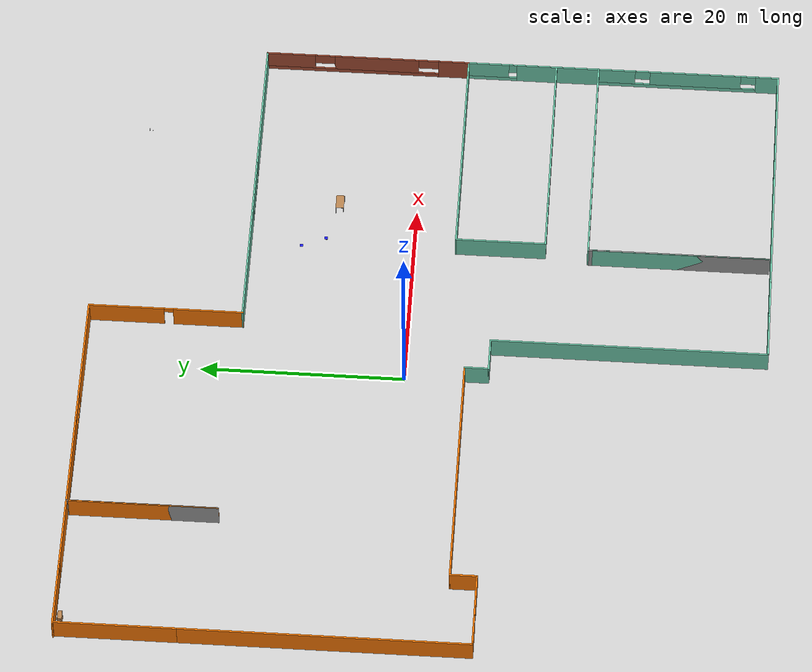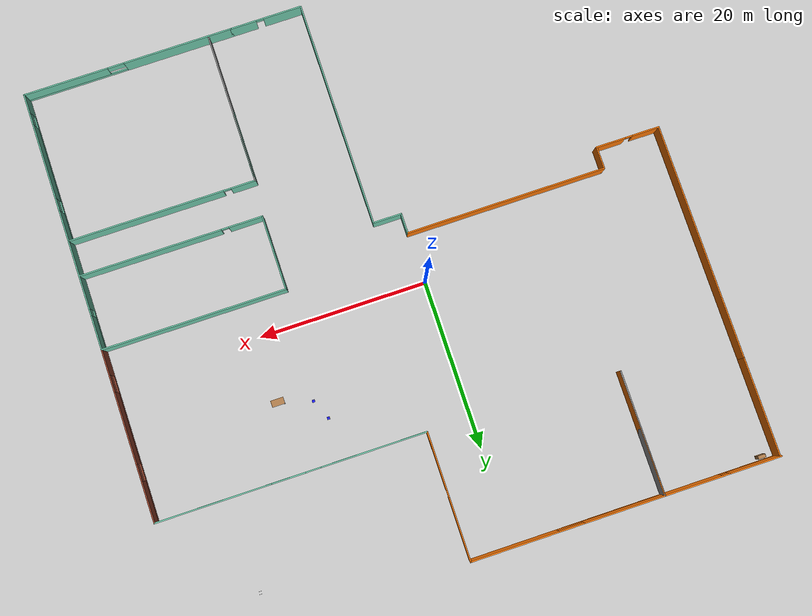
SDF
<sdf version="1.6">
 <world name="default">
  <plugin name="welcome_message" filename="libwelcome_message.so"/>
  <light name="sun" type="directional">
   <pose>0 0 10 0 -0 0</pose>
   <diffuse>0.8 0.8 0.8 1</diffuse>
   <specular>0.2 0.2 0.2 1</specular>
   <attenuation>
    <range>1000</range>
    <constant>0.9</constant>
    <linear>0.01</linear>
    <quadratic>0.001</quadratic>
   </attenuation>
   <direction>-0.5 0.1 -0.9</direction>
  </light>
  <model name="ground_plane">
   <static>1</static>
   <link name="link">
    <collision name="collision">
     <geometry><plane><normal>0 0 1</normal><size>100 100</size></plane></geometry>
     <surface>
      <contact><collide_bitmask>65535</collide_bitmask></contact>
      <friction><ode><mu>100</mu><mu2>50</mu2></ode></friction>
     </surface>
    </collision>
    <visual name="visual">
     <cast_shadows>0</cast_shadows>
     <geometry><plane><normal>0 0 1</normal><size>100 100</size></plane></geometry>
     <material>
      <script><uri>file://media/materials/scripts/gazebo.material</uri><name>Gazebo/Grey</name></script>
     </material>
    </visual>
   </link>
  </model>
  <gravity>0 0 -9.8</gravity>
  <magnetic_field>6e-06 2.3e-05 -4.2e-05</magnetic_field>
  <atmosphere type="adiabatic"/>
  <physics name="default_physics" default="0" type="ode">
   <max_step_size>0.001</max_step_size>
   <real_time_factor>1</real_time_factor>
   <real_time_update_rate>1000</real_time_update_rate>
  </physics>
  <scene><ambient>0.4 0.4 0.4 1</ambient><background>0.7 0.7 0.7 1</background><shadows>1</shadows></scene>
  <spherical_coordinates>
   <surface_model>EARTH_WGS84</surface_model>
   <latitude_deg>0</latitude_deg>
   <longitude_deg>0</longitude_deg>
   <elevation>0</elevation>
   <heading_deg>0</heading_deg>
  </spherical_coordinates>
  <model name="building1">
   <pose>2.8843 -1.97126 0 0 -0 0</pose>
   <link name="Wall_0">
    <collision name="Wall_0_Collision">
     <geometry><box><size>28.25 0.15 2.5</size></box></geometry>
     <pose>0 0 1.25 0 -0 0</pose>
    </collision>
    <visual name="Wall_0_Visual">
     <pose>0 0 1.25 0 -0 0</pose>
     <geometry><box><size>28.25 0.15 2.5</size></box></geometry>
     <material>
      <script><uri>file://media/materials/scripts/gazebo.material</uri><name>Gazebo/Grey</name></script>
      <ambient>0.996078 0.47451 0.0196078 1</ambient>
     </material>
     <meta><layer>0</layer></meta>
    </visual>
    <pose>-34.175 7.575 0 0 0 -1.5708</pose>
   </link>
   <link name="Wall_1">
    <pose>-30.375 -6.475 0 0 -0 0</pose>
    <visual name="Wall_1_Visual_0">
     <pose>-2.22971 0 1.25 0 -0 0</pose>
     <geometry><box><size>3.29058 0.15 2.5</size></box></geometry>
     <material>
      <script><uri>file://media/materials/scripts/gazebo.material</uri><name>Gazebo/Grey</name></script>
      <ambient>0.996078 0.47451 0.0196078 1</ambient>
     </material>
     <meta><layer>0</layer></meta>
    </visual>
    <collision name="Wall_1_Collision_0">
     <geometry><box><size>3.29058 0.15 2.5</size></box></geometry>
     <pose>-2.22971 0 1.25 0 -0 0</pose>
    </collision>
    <visual name="Wall_1_Visual_1">
     <pose>2.09529 0 1.25 0 -0 0</pose>
     <geometry><box><size>3.55942 0.15 2.5</size></box></geometry>
     <material>
      <script><uri>file://media/materials/scripts/gazebo.material</uri><name>Gazebo/Grey</name></script>
      <ambient>0.996078 0.47451 0.0196078 1</ambient>
     </material>
     <meta><layer>0</layer></meta>
    </visual>
    <collision name="Wall_1_Collision_1">
     <geometry><box><size>3.55942 0.15 2.5</size></box></geometry>
     <pose>2.09529 0 1.25 0 -0 0</pose>
    </collision>
    <visual name="Wall_1_Visual_2">
     <pose>-0.134418 0 2.25 0 -0 0</pose>
     <geometry><box><size>0.9 0.15 0.5</size></box></geometry>
     <material>
      <script><uri>file://media/materials/scripts/gazebo.material</uri><name>Gazebo/Grey</name></script>
      <ambient>0.996078 0.47451 0.0196078 1</ambient>
     </material>
     <meta><layer>0</layer></meta>
    </visual>
    <collision name="Wall_1_Collision_2">
     <geometry><box><size>0.9 0.15 0.5</size></box></geometry>
     <pose>-0.134418 0 2.25 0 -0 0</pose>
    </collision>
   </link>
   <link name="Wall_10">
    <pose>23.15 -15.225 0 0 -0 3.14159</pose>
    <visual name="Wall_10_Visual_0">
     <pose>-1.95259 0 1.25 0 -0 0</pose>
     <geometry><box><size>18.5948 0.15 2.5</size></box></geometry>
     <material>
      <script><uri>file://media/materials/scripts/gazebo.material</uri><name>Gazebo/Grey</name></script>
      <ambient>0.435294 0.796078 0.67451 1</ambient>
     </material>
     <meta><layer>0</layer></meta>
    </visual>
    <collision name="Wall_10_Collision_0">
     <geometry><box><size>18.5948 0.15 2.5</size></box></geometry>
     <pose>-1.95259 0 1.25 0 -0 0</pose>
    </collision>
    <visual name="Wall_10_Visual_1">
     <pose>9.74741 0 1.25 0 -0 0</pose>
     <geometry><box><size>3.00517 0.15 2.5</size></box></geometry>
     <material>
      <script><uri>file://media/materials/scripts/gazebo.material</uri><name>Gazebo/Grey</name></script>
      <ambient>0.435294 0.796078 0.67451 1</ambient>
     </material>
     <meta><layer>0</layer></meta>
    </visual>
    <collision name="Wall_10_Collision_1">
     <geometry><box><size>3.00517 0.15 2.5</size></box></geometry>
     <pose>9.74741 0 1.25 0 -0 0</pose>
    </collision>
    <visual name="Wall_10_Visual_2">
     <pose>7.79483 0 2.25 0 -0 0</pose>
     <geometry><box><size>0.9 0.15 0.5</size></box></geometry>
     <material>
      <script><uri>file://media/materials/scripts/gazebo.material</uri><name>Gazebo/Grey</name></script>
      <ambient>0.435294 0.796078 0.67451 1</ambient>
     </material>
     <meta><layer>0</layer></meta>
    </visual>
    <collision name="Wall_10_Collision_2">
     <geometry><box><size>0.9 0.15 0.5</size></box></geometry>
     <pose>7.79483 0 2.25 0 -0 0</pose>
    </collision>
   </link>
   <link name="Wall_11">
    <collision name="Wall_11_Collision">
     <geometry><box><size>18 0.15 2.5</size></box></geometry>
     <pose>0 0 1.25 0 -0 0</pose>
    </collision>
    <visual name="Wall_11_Visual">
     <pose>0 0 1.25 0 -0 0</pose>
     <geometry><box><size>18 0.15 2.5</size></box></geometry>
     <material>
      <script><uri>file://media/materials/scripts/gazebo.material</uri><name>Gazebo/Grey</name></script>
      <ambient>1 1 1 1</ambient>
     </material>
     <meta><layer>0</layer></meta>
    </visual>
    <pose>11.975 -24.15 0 0 0 -1.5708</pose>
   </link>
   <link name="Wall_12">
    <collision name="Wall_12_Collision">
     <geometry><box><size>17.5 0.15 2.5</size></box></geometry>
     <pose>0 0 1.25 0 -0 0</pose>
    </collision>
    <visual name="Wall_12_Visual">
     <pose>0 0 1.25 0 -0 0</pose>
     <geometry><box><size>17.5 0.15 2.5</size></box></geometry>
     <material>
      <script><uri>file://media/materials/scripts/gazebo.material</uri><name>Gazebo/Grey</name></script>
      <ambient>0.435294 0.796078 0.67451 1</ambient>
     </material>
     <meta><layer>0</layer></meta>
    </visual>
    <pose>11.975 -24.4 0 0 -0 1.5708</pose>
   </link>
   <link name="Wall_14">
    <pose>34.325 -8.675 0 0 -0 1.5708</pose>
    <visual name="Wall_14_Visual_0">
     <pose>-2.47216 0 1.25 0 -0 0</pose>
     <geometry><box><size>8.30568 0.15 2.5</size></box></geometry>
     <material>
      <script><uri>file://media/materials/scripts/gazebo.material</uri><name>Gazebo/Grey</name></script>
      <ambient>0.435294 0.796078 0.67451 1</ambient>
     </material>
     <meta><layer>0</layer></meta>
    </visual>
    <collision name="Wall_14_Collision_0">
     <geometry><box><size>8.30568 0.15 2.5</size></box></geometry>
     <pose>-2.47216 0 1.25 0 -0 0</pose>
    </collision>
    <visual name="Wall_14_Visual_1">
     <pose>4.15284 0 0.25 0 -0 0</pose>
     <geometry><box><size>4.94432 0.15 0.5</size></box></geometry>
     <material>
      <script><uri>file://media/materials/scripts/gazebo.material</uri><name>Gazebo/Grey</name></script>
      <ambient>0.435294 0.796078 0.67451 1</ambient>
     </material>
     <meta><layer>0</layer></meta>
    </visual>
    <collision name="Wall_14_Collision_1">
     <geometry><box><size>4.94432 0.15 0.5</size></box></geometry>
     <pose>4.15284 0 0.25 0 -0 0</pose>
    </collision>
    <visual name="Wall_14_Visual_2">
     <pose>4.55284 0 1.5 0 -0 0</pose>
     <geometry><box><size>4.14432 0.15 2</size></box></geometry>
     <material>
      <script><uri>file://media/materials/scripts/gazebo.material</uri><name>Gazebo/Grey</name></script>
      <ambient>0.435294 0.796078 0.67451 1</ambient>
     </material>
     <meta><layer>0</layer></meta>
    </visual>
    <collision name="Wall_14_Collision_2">
     <geometry><box><size>4.14432 0.15 2</size></box></geometry>
     <pose>4.55284 0 1.5 0 -0 0</pose>
    </collision>
    <visual name="Wall_14_Visual_3">
     <pose>2.08068 0 1.9 0 -0 0</pose>
     <geometry><box><size>0.8 0.15 1.2</size></box></geometry>
     <material>
      <script><uri>file://media/materials/scripts/gazebo.material</uri><name>Gazebo/Grey</name></script>
      <ambient>0.435294 0.796078 0.67451 1</ambient>
     </material>
     <meta><layer>0</layer></meta>
    </visual>
    <collision name="Wall_14_Collision_3">
     <geometry><box><size>0.8 0.15 1.2</size></box></geometry>
     <pose>2.08068 0 1.9 0 -0 0</pose>
    </collision>
   </link>
   <link name="Wall_15">
    <collision name="Wall_15_Collision">
     <geometry><box><size>22 0.15 2.5</size></box></geometry>
     <pose>0 0 1.25 0 -0 0</pose>
    </collision>
    <visual name="Wall_15_Visual">
     <pose>0 0 1.25 0 -0 0</pose>
     <geometry><box><size>22 0.15 2.5</size></box></geometry>
     <material>
      <script><uri>file://media/materials/scripts/gazebo.material</uri><name>Gazebo/Grey</name></script>
      <ambient>0.435294 0.796078 0.67451 1</ambient>
     </material>
     <meta><layer>0</layer></meta>
    </visual>
    <pose>23.4 -2.125 0 0 -0 3.14159</pose>
   </link>
   <link name="Wall_16">
    <collision name="Wall_16_Collision">
     <geometry><box><size>9 0.15 2.5</size></box></geometry>
     <pose>0 0 1.25 0 -0 0</pose>
    </collision>
    <visual name="Wall_16_Visual">
     <pose>0 0 1.25 0 -0 0</pose>
     <geometry><box><size>9 0.15 2.5</size></box></geometry>
     <material>
      <script><uri>file://media/materials/scripts/gazebo.material</uri><name>Gazebo/Grey</name></script>
      <ambient>0.435294 0.796078 0.67451 1</ambient>
     </material>
     <meta><layer>0</layer></meta>
    </visual>
    <pose>12.475 -6.55 0 0 0 -1.5708</pose>
   </link>
   <link name="Wall_17">
    <pose>23.4 -10.975 0 0 -0 0</pose>
    <visual name="Wall_17_Visual_0">
     <pose>-8.94755 0 1.25 0 -0 0</pose>
     <geometry><box><size>4.1049 0.15 2.5</size></box></geometry>
     <material>
      <script><uri>file://media/materials/scripts/gazebo.material</uri><name>Gazebo/Grey</name></script>
      <ambient>0.435294 0.796078 0.67451 1</ambient>
     </material>
     <meta><layer>0</layer></meta>
    </visual>
    <collision name="Wall_17_Collision_0">
     <geometry><box><size>4.1049 0.15 2.5</size></box></geometry>
     <pose>-8.94755 0 1.25 0 -0 0</pose>
    </collision>
    <visual name="Wall_17_Visual_1">
     <pose>2.50245 0 1.25 0 -0 0</pose>
     <geometry><box><size>16.9951 0.15 2.5</size></box></geometry>
     <material>
      <script><uri>file://media/materials/scripts/gazebo.material</uri><name>Gazebo/Grey</name></script>
      <ambient>0.435294 0.796078 0.67451 1</ambient>
     </material>
     <meta><layer>0</layer></meta>
    </visual>
    <collision name="Wall_17_Collision_1">
     <geometry><box><size>16.9951 0.15 2.5</size></box></geometry>
     <pose>2.50245 0 1.25 0 -0 0</pose>
    </collision>
    <visual name="Wall_17_Visual_2">
     <pose>-6.4451 0 2.25 0 -0 0</pose>
     <geometry><box><size>0.9 0.15 0.5</size></box></geometry>
     <material>
      <script><uri>file://media/materials/scripts/gazebo.material</uri><name>Gazebo/Grey</name></script>
      <ambient>0.435294 0.796078 0.67451 1</ambient>
     </material>
     <meta><layer>0</layer></meta>
    </visual>
    <collision name="Wall_17_Collision_2">
     <geometry><box><size>0.9 0.15 0.5</size></box></geometry>
     <pose>-6.4451 0 2.25 0 -0 0</pose>
    </collision>
   </link>
   <link name="Wall_19">
    <pose>34.325 8.05 0 0 -0 1.5708</pose>
    <visual name="Wall_19_Visual_0">
     <pose>-8.69186 0 1.25 0 -0 0</pose>
     <geometry><box><size>3.11628 0.15 2.5</size></box></geometry>
     <material>
      <script><uri>file://media/materials/scripts/gazebo.material</uri><name>Gazebo/Bricks</name></script>
      <ambient>0.435294 0.796078 0.67451 1</ambient>
     </material>
     <meta><layer>0</layer></meta>
    </visual>
    <collision name="Wall_19_Collision_0">
     <geometry><box><size>3.11628 0.15 2.5</size></box></geometry>
     <pose>-8.69186 0 1.25 0 -0 0</pose>
    </collision>
    <visual name="Wall_19_Visual_1">
     <pose>1.55814 0 0.25 0 -0 0</pose>
     <geometry><box><size>17.3837 0.15 0.5</size></box></geometry>
     <material>
      <script><uri>file://media/materials/scripts/gazebo.material</uri><name>Gazebo/Bricks</name></script>
      <ambient>0.435294 0.796078 0.67451 1</ambient>
     </material>
     <meta><layer>0</layer></meta>
    </visual>
    <collision name="Wall_19_Collision_1">
     <geometry><box><size>17.3837 0.15 0.5</size></box></geometry>
     <pose>1.55814 0 0.25 0 -0 0</pose>
    </collision>
    <visual name="Wall_19_Visual_2">
     <pose>-0.896427 0 1.5 0 -0 0</pose>
     <geometry><box><size>8.47458 0.15 2</size></box></geometry>
     <material>
      <script><uri>file://media/materials/scripts/gazebo.material</uri><name>Gazebo/Bricks</name></script>
      <ambient>0.435294 0.796078 0.67451 1</ambient>
     </material>
     <meta><layer>0</layer></meta>
    </visual>
    <collision name="Wall_19_Collision_2">
     <geometry><box><size>8.47458 0.15 2</size></box></geometry>
     <pose>-0.896427 0 1.5 0 -0 0</pose>
    </collision>
    <visual name="Wall_19_Visual_3">
     <pose>7.79543 0 1.5 0 -0 0</pose>
     <geometry><box><size>4.90914 0.15 2</size></box></geometry>
     <material>
      <script><uri>file://media/materials/scripts/gazebo.material</uri><name>Gazebo/Bricks</name></script>
      <ambient>0.435294 0.796078 0.67451 1</ambient>
     </material>
     <meta><layer>0</layer></meta>
    </visual>
    <collision name="Wall_19_Collision_3">
     <geometry><box><size>4.90914 0.15 2</size></box></geometry>
     <pose>7.79543 0 1.5 0 -0 0</pose>
    </collision>
    <visual name="Wall_19_Visual_4">
     <pose>-6.13372 0 1.9 0 -0 0</pose>
     <geometry><box><size>2 0.15 1.2</size></box></geometry>
     <material>
      <script><uri>file://media/materials/scripts/gazebo.material</uri><name>Gazebo/Bricks</name></script>
      <ambient>0.435294 0.796078 0.67451 1</ambient>
     </material>
     <meta><layer>0</layer></meta>
    </visual>
    <collision name="Wall_19_Collision_4">
     <geometry><box><size>2 0.15 1.2</size></box></geometry>
     <pose>-6.13372 0 1.9 0 -0 0</pose>
    </collision>
    <visual name="Wall_19_Visual_5">
     <pose>4.34086 0 1.9 0 -0 0</pose>
     <geometry><box><size>2 0.15 1.2</size></box></geometry>
     <material>
      <script><uri>file://media/materials/scripts/gazebo.material</uri><name>Gazebo/Bricks</name></script>
      <ambient>0.435294 0.796078 0.67451 1</ambient>
     </material>
     <meta><layer>0</layer></meta>
    </visual>
    <collision name="Wall_19_Collision_5">
     <geometry><box><size>2 0.15 1.2</size></box></geometry>
     <pose>4.34086 0 1.9 0 -0 0</pose>
    </collision>
   </link>
   <link name="Wall_2">
    <collision name="Wall_2_Collision">
     <geometry><box><size>2.75 0.15 2.5</size></box></geometry>
     <pose>0 0 1.25 0 -0 0</pose>
    </collision>
    <visual name="Wall_2_Visual">
     <pose>0 0 1.25 0 -0 0</pose>
     <geometry><box><size>2.75 0.15 2.5</size></box></geometry>
     <material>
      <script><uri>file://media/materials/scripts/gazebo.material</uri><name>Gazebo/Grey</name></script>
      <ambient>0.996078 0.47451 0.0196078 1</ambient>
     </material>
     <meta><layer>0</layer></meta>
    </visual>
    <pose>-26.575 -5.175 0 0 -0 1.5708</pose>
   </link>
   <link name="Wall_20">
    <pose>24.65 18.225 0 0 -0 3.14159</pose>
    <visual name="Wall_20_Visual_0">
     <pose>-2.88254 0 1.25 0 -0 0</pose>
     <geometry><box><size>13.7349 0.15 2.5</size></box></geometry>
     <material>
      <script><uri>file://media/materials/scripts/gazebo.material</uri><name>Gazebo/Grey</name></script>
      <ambient>0.435294 0.796078 0.67451 1</ambient>
     </material>
     <meta><layer>0</layer></meta>
    </visual>
    <collision name="Wall_20_Collision_0">
     <geometry><box><size>13.7349 0.15 2.5</size></box></geometry>
     <pose>-2.88254 0 1.25 0 -0 0</pose>
    </collision>
    <visual name="Wall_20_Visual_1">
     <pose>6.86746 0 0.25 0 -0 0</pose>
     <geometry><box><size>5.76509 0.15 0.5</size></box></geometry>
     <material>
      <script><uri>file://media/materials/scripts/gazebo.material</uri><name>Gazebo/Grey</name></script>
      <ambient>0.435294 0.796078 0.67451 1</ambient>
     </material>
     <meta><layer>0</layer></meta>
    </visual>
    <collision name="Wall_20_Collision_1">
     <geometry><box><size>5.76509 0.15 0.5</size></box></geometry>
     <pose>6.86746 0 0.25 0 -0 0</pose>
    </collision>
    <visual name="Wall_20_Visual_2">
     <pose>8.86746 0 1.5 0 -0 0</pose>
     <geometry><box><size>1.76509 0.15 2</size></box></geometry>
     <material>
      <script><uri>file://media/materials/scripts/gazebo.material</uri><name>Gazebo/Grey</name></script>
      <ambient>0.435294 0.796078 0.67451 1</ambient>
     </material>
     <meta><layer>0</layer></meta>
    </visual>
    <collision name="Wall_20_Collision_2">
     <geometry><box><size>1.76509 0.15 2</size></box></geometry>
     <pose>8.86746 0 1.5 0 -0 0</pose>
    </collision>
    <visual name="Wall_20_Visual_3">
     <pose>5.98491 0 1.9 0 -0 0</pose>
     <geometry><box><size>4 0.15 1.2</size></box></geometry>
     <material>
      <script><uri>file://media/materials/scripts/gazebo.material</uri><name>Gazebo/Grey</name></script>
      <ambient>0.435294 0.796078 0.67451 1</ambient>
     </material>
     <meta><layer>0</layer></meta>
    </visual>
    <collision name="Wall_20_Collision_3">
     <geometry><box><size>4 0.15 1.2</size></box></geometry>
     <pose>5.98491 0 1.9 0 -0 0</pose>
    </collision>
   </link>
   <link name="Wall_21">
    <collision name="Wall_21_Collision">
     <geometry><box><size>12.75 0.15 2.5</size></box></geometry>
     <pose>0 0 1.25 0 -0 0</pose>
    </collision>
    <visual name="Wall_21_Visual">
     <pose>0 0 1.25 0 -0 0</pose>
     <geometry><box><size>12.75 0.15 2.5</size></box></geometry>
     <material>
      <script><uri>file://media/materials/scripts/gazebo.material</uri><name>Gazebo/Grey</name></script>
      <ambient>0.435294 0.796078 0.67451 1</ambient>
     </material>
     <meta><layer>0</layer></meta>
    </visual>
    <pose>8.675 18.225 0 0 -0 3.14159</pose>
   </link>
   <link name="Wall_22">
    <pose>2.375 25.775 0 0 -0 1.5708</pose>
    <visual name="Wall_22_Visual_0">
     <pose>-4.18684 0 1.25 0 -0 0</pose>
     <geometry><box><size>6.87632 0.15 2.5</size></box></geometry>
     <material>
      <script><uri>file://media/materials/scripts/gazebo.material</uri><name>Gazebo/Grey</name></script>
      <ambient>0.996078 0.47451 0.0196078 1</ambient>
     </material>
     <meta><layer>0</layer></meta>
    </visual>
    <collision name="Wall_22_Collision_0">
     <geometry><box><size>6.87632 0.15 2.5</size></box></geometry>
     <pose>-4.18684 0 1.25 0 -0 0</pose>
    </collision>
    <visual name="Wall_22_Visual_1">
     <pose>3.88816 0 1.25 0 -0 0</pose>
     <geometry><box><size>7.47368 0.15 2.5</size></box></geometry>
     <material>
      <script><uri>file://media/materials/scripts/gazebo.material</uri><name>Gazebo/Grey</name></script>
      <ambient>0.996078 0.47451 0.0196078 1</ambient>
     </material>
     <meta><layer>0</layer></meta>
    </visual>
    <collision name="Wall_22_Collision_1">
     <geometry><box><size>7.47368 0.15 2.5</size></box></geometry>
     <pose>3.88816 0 1.25 0 -0 0</pose>
    </collision>
    <visual name="Wall_22_Visual_2">
     <pose>-0.298676 0 2.25 0 -0 0</pose>
     <geometry><box><size>0.9 0.15 0.5</size></box></geometry>
     <material>
      <script><uri>file://media/materials/scripts/gazebo.material</uri><name>Gazebo/Grey</name></script>
      <ambient>0.996078 0.47451 0.0196078 1</ambient>
     </material>
     <meta><layer>0</layer></meta>
    </visual>
    <collision name="Wall_22_Collision_2">
     <geometry><box><size>0.9 0.15 0.5</size></box></geometry>
     <pose>-0.298676 0 2.25 0 -0 0</pose>
    </collision>
   </link>
   <link name="Wall_23">
    <pose>-9.05 33.325 0 0 -0 3.14159</pose>
    <visual name="Wall_23_Visual_0">
     <pose>-6.28232 0 1.25 0 -0 0</pose>
     <geometry><box><size>10.4354 0.15 2.5</size></box></geometry>
     <material>
      <script><uri>file://media/materials/scripts/gazebo.material</uri><name>Gazebo/Grey</name></script>
      <ambient>0.996078 0.47451 0.0196078 1</ambient>
     </material>
     <meta><layer>0</layer></meta>
    </visual>
    <collision name="Wall_23_Collision_0">
     <geometry><box><size>10.4354 0.15 2.5</size></box></geometry>
     <pose>-6.28232 0 1.25 0 -0 0</pose>
    </collision>
    <visual name="Wall_23_Visual_1">
     <pose>5.21768 0 0.25 0 -0 0</pose>
     <geometry><box><size>12.5646 0.15 0.5</size></box></geometry>
     <material>
      <script><uri>file://media/materials/scripts/gazebo.material</uri><name>Gazebo/Grey</name></script>
      <ambient>0.996078 0.47451 0.0196078 1</ambient>
     </material>
     <meta><layer>0</layer></meta>
    </visual>
    <collision name="Wall_23_Collision_1">
     <geometry><box><size>12.5646 0.15 0.5</size></box></geometry>
     <pose>5.21768 0 0.25 0 -0 0</pose>
    </collision>
    <visual name="Wall_23_Visual_2">
     <pose>6.71768 0 1.5 0 -0 0</pose>
     <geometry><box><size>9.56464 0.15 2</size></box></geometry>
     <material>
      <script><uri>file://media/materials/scripts/gazebo.material</uri><name>Gazebo/Grey</name></script>
      <ambient>0.996078 0.47451 0.0196078 1</ambient>
     </material>
     <meta><layer>0</layer></meta>
    </visual>
    <collision name="Wall_23_Collision_2">
     <geometry><box><size>9.56464 0.15 2</size></box></geometry>
     <pose>6.71768 0 1.5 0 -0 0</pose>
    </collision>
    <visual name="Wall_23_Visual_3">
     <pose>0.435356 0 1.9 0 -0 0</pose>
     <geometry><box><size>3 0.15 1.2</size></box></geometry>
     <material>
      <script><uri>file://media/materials/scripts/gazebo.material</uri><name>Gazebo/Grey</name></script>
      <ambient>0.996078 0.47451 0.0196078 1</ambient>
     </material>
     <meta><layer>0</layer></meta>
    </visual>
    <collision name="Wall_23_Collision_3">
     <geometry><box><size>3 0.15 1.2</size></box></geometry>
     <pose>0.435356 0 1.9 0 -0 0</pose>
    </collision>
   </link>
   <link name="Wall_24">
    <collision name="Wall_24_Collision">
     <geometry><box><size>14.75 0.15 2.5</size></box></geometry>
     <pose>0 0 1.25 0 -0 0</pose>
    </collision>
    <visual name="Wall_24_Visual">
     <pose>0 0 1.25 0 -0 0</pose>
     <geometry><box><size>14.75 0.15 2.5</size></box></geometry>
     <material>
      <script><uri>file://media/materials/scripts/gazebo.material</uri><name>Gazebo/Grey</name></script>
      <ambient>1 1 1 1</ambient>
     </material>
     <meta><layer>0</layer></meta>
    </visual>
    <pose>-20.475 26.025 0 0 0 -1.5708</pose>
   </link>
   <link name="Wall_25">
    <collision name="Wall_25_Collision">
     <geometry><box><size>14.5 0.15 2.5</size></box></geometry>
     <pose>0 0 1.25 0 -0 0</pose>
    </collision>
    <visual name="Wall_25_Visual">
     <pose>0 0 1.25 0 -0 0</pose>
     <geometry><box><size>14.5 0.15 2.5</size></box></geometry>
     <material>
      <script><uri>file://media/materials/scripts/gazebo.material</uri><name>Gazebo/Grey</name></script>
      <ambient>0.996078 0.47451 0.0196078 1</ambient>
     </material>
     <meta><layer>0</layer></meta>
    </visual>
    <pose>-20.475 25.9 0 0 -0 1.5708</pose>
   </link>
   <link name="Wall_26">
    <collision name="Wall_26_Collision">
     <geometry><box><size>0.4 0.15 2.5</size></box></geometry>
     <pose>0 0 1.25 0 -0 0</pose>
    </collision>
    <visual name="Wall_26_Visual">
     <pose>0 0 1.25 0 -0 0</pose>
     <geometry><box><size>0.4 0.15 2.5</size></box></geometry>
     <material>
      <script><uri>file://media/materials/scripts/gazebo.material</uri><name>Gazebo/Grey</name></script>
      <ambient>1 1 1 1</ambient>
     </material>
     <meta><layer>0</layer></meta>
    </visual>
    <pose>-20.475 33.2 0 0 -0 1.5708</pose>
   </link>
   <link name="Wall_27">
    <pose>-27.4 33.325 0 0 -0 3.14159</pose>
    <visual name="Wall_27_Visual_0">
     <pose>-3.49206 0 1.25 0 -0 0</pose>
     <geometry><box><size>7.01587 0.15 2.5</size></box></geometry>
     <material>
      <script><uri>file://media/materials/scripts/gazebo.material</uri><name>Gazebo/Grey</name></script>
      <ambient>0.996078 0.47451 0.0196078 1</ambient>
     </material>
     <meta><layer>0</layer></meta>
    </visual>
    <collision name="Wall_27_Collision_0">
     <geometry><box><size>7.01587 0.15 2.5</size></box></geometry>
     <pose>-3.49206 0 1.25 0 -0 0</pose>
    </collision>
    <visual name="Wall_27_Visual_1">
     <pose>3.50794 0 0.25 0 -0 0</pose>
     <geometry><box><size>6.98413 0.15 0.5</size></box></geometry>
     <material>
      <script><uri>file://media/materials/scripts/gazebo.material</uri><name>Gazebo/Grey</name></script>
      <ambient>0.996078 0.47451 0.0196078 1</ambient>
     </material>
     <meta><layer>0</layer></meta>
    </visual>
    <collision name="Wall_27_Collision_1">
     <geometry><box><size>6.98413 0.15 0.5</size></box></geometry>
     <pose>3.50794 0 0.25 0 -0 0</pose>
    </collision>
    <visual name="Wall_27_Visual_2">
     <pose>3.90794 0 1.5 0 -0 0</pose>
     <geometry><box><size>6.18413 0.15 2</size></box></geometry>
     <material>
      <script><uri>file://media/materials/scripts/gazebo.material</uri><name>Gazebo/Grey</name></script>
      <ambient>0.996078 0.47451 0.0196078 1</ambient>
     </material>
     <meta><layer>0</layer></meta>
    </visual>
    <collision name="Wall_27_Collision_2">
     <geometry><box><size>6.18413 0.15 2</size></box></geometry>
     <pose>3.90794 0 1.5 0 -0 0</pose>
    </collision>
    <visual name="Wall_27_Visual_3">
     <pose>0.415874 0 1.9 0 -0 0</pose>
     <geometry><box><size>0.8 0.15 1.2</size></box></geometry>
     <material>
      <script><uri>file://media/materials/scripts/gazebo.material</uri><name>Gazebo/Grey</name></script>
      <ambient>0.996078 0.47451 0.0196078 1</ambient>
     </material>
     <meta><layer>0</layer></meta>
    </visual>
    <collision name="Wall_27_Collision_3">
     <geometry><box><size>0.8 0.15 1.2</size></box></geometry>
     <pose>0.415874 0 1.9 0 -0 0</pose>
    </collision>
   </link>
   <link name="Wall_3">
    <collision name="Wall_3_Collision">
     <geometry><box><size>24 0.15 2.5</size></box></geometry>
     <pose>0 0 1.25 0 -0 0</pose>
    </collision>
    <visual name="Wall_3_Visual">
     <pose>0 0 1.25 0 -0 0</pose>
     <geometry><box><size>24 0.15 2.5</size></box></geometry>
     <material>
      <script><uri>file://media/materials/scripts/gazebo.material</uri><name>Gazebo/Grey</name></script>
      <ambient>0.996078 0.47451 0.0196078 1</ambient>
     </material>
     <meta><layer>0</layer></meta>
    </visual>
    <pose>-14.65 -3.875 0 0 -0 0</pose>
   </link>
   <link name="Wall_30">
    <collision name="Wall_30_Collision">
     <geometry><box><size>11.75 0.15 2.5</size></box></geometry>
     <pose>0 0 1.25 0 -0 0</pose>
    </collision>
    <visual name="Wall_30_Visual">
     <pose>0 0 1.25 0 -0 0</pose>
     <geometry><box><size>11.75 0.15 2.5</size></box></geometry>
     <material>
      <script><uri>file://media/materials/scripts/gazebo.material</uri><name>Gazebo/Grey</name></script>
      <ambient>0.996078 0.47451 0.0196078 1</ambient>
     </material>
     <meta><layer>0</layer></meta>
    </visual>
    <pose>-34.175 27.425 0 0 -0 1.5708</pose>
   </link>
   <link name="Wall_4">
    <collision name="Wall_4_Collision">
     <geometry><box><size>2.5 0.15 2.5</size></box></geometry>
     <pose>0 0 1.25 0 -0 0</pose>
    </collision>
    <visual name="Wall_4_Visual">
     <pose>0 0 1.25 0 -0 0</pose>
     <geometry><box><size>2.5 0.15 2.5</size></box></geometry>
     <material>
      <script><uri>file://media/materials/scripts/gazebo.material</uri><name>Gazebo/Grey</name></script>
      <ambient>0.435294 0.796078 0.67451 1</ambient>
     </material>
     <meta><layer>0</layer></meta>
    </visual>
    <pose>-2.725 -5.05 0 0 0 -1.5708</pose>
   </link>
   <link name="Wall_5">
    <collision name="Wall_5_Collision">
     <geometry><box><size>3.5 0.15 2.5</size></box></geometry>
     <pose>0 0 1.25 0 -0 0</pose>
    </collision>
    <visual name="Wall_5_Visual">
     <pose>0 0 1.25 0 -0 0</pose>
     <geometry><box><size>3.5 0.15 2.5</size></box></geometry>
     <material>
      <script><uri>file://media/materials/scripts/gazebo.material</uri><name>Gazebo/Grey</name></script>
      <ambient>0.435294 0.796078 0.67451 1</ambient>
     </material>
     <meta><layer>0</layer></meta>
    </visual>
    <pose>-1.05 -6.225 0 0 -0 0</pose>
   </link>
   <link name="Wall_6">
    <collision name="Wall_6_Collision">
     <geometry><box><size>27.25 0.15 2.5</size></box></geometry>
     <pose>0 0 1.25 0 -0 0</pose>
    </collision>
    <visual name="Wall_6_Visual">
     <pose>0 0 1.25 0 -0 0</pose>
     <geometry><box><size>27.25 0.15 2.5</size></box></geometry>
     <material>
      <script><uri>file://media/materials/scripts/gazebo.material</uri><name>Gazebo/Grey</name></script>
      <ambient>0.435294 0.796078 0.67451 1</ambient>
     </material>
     <meta><layer>0</layer></meta>
    </visual>
    <pose>0.625002 -19.775 0 0 0 -1.5708</pose>
   </link>
   <link name="Wall_7">
    <pose>4.925 -33.325 0 0 -0 0</pose>
    <visual name="Wall_7_Visual_0">
     <pose>-2.04468 0 1.25 0 -0 0</pose>
     <geometry><box><size>4.66063 0.15 2.5</size></box></geometry>
     <material>
      <script><uri>file://media/materials/scripts/gazebo.material</uri><name>Gazebo/Grey</name></script>
      <ambient>0.435294 0.796078 0.67451 1</ambient>
     </material>
     <meta><layer>0</layer></meta>
    </visual>
    <collision name="Wall_7_Collision_0">
     <geometry><box><size>4.66063 0.15 2.5</size></box></geometry>
     <pose>-2.04468 0 1.25 0 -0 0</pose>
    </collision>
    <visual name="Wall_7_Visual_1">
     <pose>2.78031 0 1.25 0 -0 0</pose>
     <geometry><box><size>3.18937 0.15 2.5</size></box></geometry>
     <material>
      <script><uri>file://media/materials/scripts/gazebo.material</uri><name>Gazebo/Grey</name></script>
      <ambient>0.435294 0.796078 0.67451 1</ambient>
     </material>
     <meta><layer>0</layer></meta>
    </visual>
    <collision name="Wall_7_Collision_1">
     <geometry><box><size>3.18937 0.15 2.5</size></box></geometry>
     <pose>2.78031 0 1.25 0 -0 0</pose>
    </collision>
    <visual name="Wall_7_Visual_2">
     <pose>0.73563 0 2.25 0 -0 0</pose>
     <geometry><box><size>0.9 0.15 0.5</size></box></geometry>
     <material>
      <script><uri>file://media/materials/scripts/gazebo.material</uri><name>Gazebo/Grey</name></script>
      <ambient>0.435294 0.796078 0.67451 1</ambient>
     </material>
     <meta><layer>0</layer></meta>
    </visual>
    <collision name="Wall_7_Collision_2">
     <geometry><box><size>0.9 0.15 0.5</size></box></geometry>
     <pose>0.73563 0 2.25 0 -0 0</pose>
    </collision>
   </link>
   <link name="Wall_8">
    <pose>21.775 -33.325 0 0 -0 0</pose>
    <visual name="Wall_8_Visual_0">
     <pose>-6.07614 0 1.25 0 -0 0</pose>
     <geometry><box><size>13.0977 0.15 2.5</size></box></geometry>
     <material>
      <script><uri>file://media/materials/scripts/gazebo.material</uri><name>Gazebo/Grey</name></script>
      <ambient>0.435294 0.796078 0.67451 1</ambient>
     </material>
     <meta><layer>0</layer></meta>
    </visual>
    <collision name="Wall_8_Collision_0">
     <geometry><box><size>13.0977 0.15 2.5</size></box></geometry>
     <pose>-6.07614 0 1.25 0 -0 0</pose>
    </collision>
    <visual name="Wall_8_Visual_1">
     <pose>6.54886 0 0.25 0 -0 0</pose>
     <geometry><box><size>12.1523 0.15 0.5</size></box></geometry>
     <material>
      <script><uri>file://media/materials/scripts/gazebo.material</uri><name>Gazebo/Grey</name></script>
      <ambient>0.435294 0.796078 0.67451 1</ambient>
     </material>
     <meta><layer>0</layer></meta>
    </visual>
    <collision name="Wall_8_Collision_1">
     <geometry><box><size>12.1523 0.15 0.5</size></box></geometry>
     <pose>6.54886 0 0.25 0 -0 0</pose>
    </collision>
    <visual name="Wall_8_Visual_2">
     <pose>7.54886 0 1.5 0 -0 0</pose>
     <geometry><box><size>10.1523 0.15 2</size></box></geometry>
     <material>
      <script><uri>file://media/materials/scripts/gazebo.material</uri><name>Gazebo/Grey</name></script>
      <ambient>0.435294 0.796078 0.67451 1</ambient>
     </material>
     <meta><layer>0</layer></meta>
    </visual>
    <collision name="Wall_8_Collision_2">
     <geometry><box><size>10.1523 0.15 2</size></box></geometry>
     <pose>7.54886 0 1.5 0 -0 0</pose>
    </collision>
    <visual name="Wall_8_Visual_3">
     <pose>1.47272 0 1.9 0 -0 0</pose>
     <geometry><box><size>2 0.15 1.2</size></box></geometry>
     <material>
      <script><uri>file://media/materials/scripts/gazebo.material</uri><name>Gazebo/Grey</name></script>
      <ambient>0.435294 0.796078 0.67451 1</ambient>
     </material>
     <meta><layer>0</layer></meta>
    </visual>
    <collision name="Wall_8_Collision_3">
     <geometry><box><size>2 0.15 1.2</size></box></geometry>
     <pose>1.47272 0 1.9 0 -0 0</pose>
    </collision>
   </link>
   <link name="Wall_9">
    <pose>34.325 -24.275 0 0 -0 1.5708</pose>
    <visual name="Wall_9_Visual_0">
     <pose>-7.9629 0 1.25 0 -0 0</pose>
     <geometry><box><size>2.3242 0.15 2.5</size></box></geometry>
     <material>
      <script><uri>file://media/materials/scripts/gazebo.material</uri><name>Gazebo/Grey</name></script>
      <ambient>0.435294 0.796078 0.67451 1</ambient>
     </material>
     <meta><layer>0</layer></meta>
    </visual>
    <collision name="Wall_9_Collision_0">
     <geometry><box><size>2.3242 0.15 2.5</size></box></geometry>
     <pose>-7.9629 0 1.25 0 -0 0</pose>
    </collision>
    <visual name="Wall_9_Visual_1">
     <pose>1.1621 0 0.25 0 -0 0</pose>
     <geometry><box><size>15.9258 0.15 0.5</size></box></geometry>
     <material>
      <script><uri>file://media/materials/scripts/gazebo.material</uri><name>Gazebo/Grey</name></script>
      <ambient>0.435294 0.796078 0.67451 1</ambient>
     </material>
     <meta><layer>0</layer></meta>
    </visual>
    <collision name="Wall_9_Collision_1">
     <geometry><box><size>15.9258 0.15 0.5</size></box></geometry>
     <pose>1.1621 0 0.25 0 -0 0</pose>
    </collision>
    <visual name="Wall_9_Visual_2">
     <pose>-0.731672 0 1.5 0 -0 0</pose>
     <geometry><box><size>9.13825 0.15 2</size></box></geometry>
     <material>
      <script><uri>file://media/materials/scripts/gazebo.material</uri><name>Gazebo/Grey</name></script>
      <ambient>0.435294 0.796078 0.67451 1</ambient>
     </material>
     <meta><layer>0</layer></meta>
    </visual>
    <collision name="Wall_9_Collision_2">
     <geometry><box><size>9.13825 0.15 2</size></box></geometry>
     <pose>-0.731672 0 1.5 0 -0 0</pose>
    </collision>
    <visual name="Wall_9_Visual_3">
     <pose>7.23123 0 1.5 0 -0 0</pose>
     <geometry><box><size>3.78755 0.15 2</size></box></geometry>
     <material>
      <script><uri>file://media/materials/scripts/gazebo.material</uri><name>Gazebo/Grey</name></script>
      <ambient>0.435294 0.796078 0.67451 1</ambient>
     </material>
     <meta><layer>0</layer></meta>
    </visual>
    <collision name="Wall_9_Collision_3">
     <geometry><box><size>3.78755 0.15 2</size></box></geometry>
     <pose>7.23123 0 1.5 0 -0 0</pose>
    </collision>
    <visual name="Wall_9_Visual_4">
     <pose>-6.0508 0 1.9 0 -0 0</pose>
     <geometry><box><size>1.5 0.15 1.2</size></box></geometry>
     <material>
      <script><uri>file://media/materials/scripts/gazebo.material</uri><name>Gazebo/Grey</name></script>
      <ambient>0.435294 0.796078 0.67451 1</ambient>
     </material>
     <meta><layer>0</layer></meta>
    </visual>
    <collision name="Wall_9_Collision_4">
     <geometry><box><size>1.5 0.15 1.2</size></box></geometry>
     <pose>-6.0508 0 1.9 0 -0 0</pose>
    </collision>
    <visual name="Wall_9_Visual_5">
     <pose>4.58745 0 1.9 0 -0 0</pose>
     <geometry><box><size>1.5 0.15 1.2</size></box></geometry>
     <material>
      <script><uri>file://media/materials/scripts/gazebo.material</uri><name>Gazebo/Grey</name></script>
      <ambient>0.435294 0.796078 0.67451 1</ambient>
     </material>
     <meta><layer>0</layer></meta>
    </visual>
    <collision name="Wall_9_Collision_5">
     <geometry><box><size>1.5 0.15 1.2</size></box></geometry>
     <pose>4.58745 0 1.9 0 -0 0</pose>
    </collision>
   </link>
   <static>1</static>
  </model>
  <model name="robot1">
   <link name="link_5">
    <pose>32.8439 32.9677 0.5 1.5707 -0 0</pose>
    <inertial>
     <mass>1</mass>
     <inertia><ixx>0.145833</ixx><ixy>0</ixy><ixz>0</ixz><iyy>0.145833</iyy><iyz>0</iyz><izz>0.125</izz></inertia>
    </inertial>
    <visual name="visual">
     <geometry><cylinder><radius>0.05</radius><length>0.02</length></cylinder></geometry>
     <material>
      <lighting>1</lighting>
      <script><uri>file://media/materials/scripts/gazebo.material</uri><name>Gazebo/Grey</name></script>
      <shader type="pixel"><normal_map>__default__</normal_map></shader>
      <ambient>0.3 0.3 0.3 1</ambient>
      <diffuse>0.7 0.7 0.7 1</diffuse>
      <specular>0.01 0.01 0.01 1</specular>
      <emissive>0 0 0 1</emissive>
     </material>
    </visual>
    <collision name="collision">
     <geometry><cylinder><radius>0.05</radius><length>0.02</length></cylinder></geometry>
     <surface>
      <friction>
       <ode><mu>1</mu><mu2>1</mu2><fdir1>0 0 0</fdir1><slip1>0</slip1><slip2>0</slip2></ode>
       <torsional>
        <coefficient>1</coefficient>
        <patch_radius>0</patch_radius>
        <surface_radius>0</surface_radius>
        <use_patch_radius>1</use_patch_radius>
        <ode><slip>0</slip></ode>
       </torsional>
      </friction>
      <bounce><restitution_coefficient>0</restitution_coefficient><threshold>1e+06</threshold></bounce>
      <contact>
       <collide_without_contact>0</collide_without_contact>
       <collide_without_contact_bitmask>1</collide_without_contact_bitmask>
       <collide_bitmask>1</collide_bitmask>
       <ode>
        <soft_cfm>0</soft_cfm>
        <soft_erp>0.2</soft_erp>
        <kp>1e+13</kp>
        <kd>1</kd>
        <max_vel>0.01</max_vel>
        <min_depth>0</min_depth>
       </ode>
       <bullet>
        <split_impulse>1</split_impulse>
        <split_impulse_penetration_threshold>-0.01</split_impulse_penetration_threshold>
        <soft_cfm>0</soft_cfm>
        <soft_erp>0.2</soft_erp>
        <kp>1e+13</kp>
        <kd>1</kd>
       </bullet>
      </contact>
     </surface>
    </collision>
   </link>
   <link name="link_5_clone">
    <pose>32.8439 33.2877 0.5 1.5707 -0 0</pose>
    <inertial>
     <mass>1</mass>
     <inertia><ixx>0.145833</ixx><ixy>0</ixy><ixz>0</ixz><iyy>0.145833</iyy><iyz>0</iyz><izz>0.125</izz></inertia>
    </inertial>
    <visual name="visual">
     <geometry><cylinder><radius>0.05</radius><length>0.02</length></cylinder></geometry>
     <material>
      <lighting>1</lighting>
      <script><uri>file://media/materials/scripts/gazebo.material</uri><name>Gazebo/Grey</name></script>
      <shader type="pixel"><normal_map>__default__</normal_map></shader>
      <ambient>0.3 0.3 0.3 1</ambient>
      <diffuse>0.7 0.7 0.7 1</diffuse>
      <specular>0.01 0.01 0.01 1</specular>
      <emissive>0 0 0 1</emissive>
     </material>
    </visual>
    <collision name="collision">
     <geometry><cylinder><radius>0.05</radius><length>0.02</length></cylinder></geometry>
     <surface>
      <friction>
       <ode><mu>1</mu><mu2>1</mu2><fdir1>0 0 0</fdir1><slip1>0</slip1><slip2>0</slip2></ode>
       <torsional>
        <coefficient>1</coefficient>
        <patch_radius>0</patch_radius>
        <surface_radius>0</surface_radius>
        <use_patch_radius>1</use_patch_radius>
        <ode><slip>0</slip></ode>
       </torsional>
      </friction>
      <bounce><restitution_coefficient>0</restitution_coefficient><threshold>1e+06</threshold></bounce>
      <contact>
       <collide_without_contact>0</collide_without_contact>
       <collide_without_contact_bitmask>1</collide_without_contact_bitmask>
       <collide_bitmask>1</collide_bitmask>
       <ode>
        <soft_cfm>0</soft_cfm>
        <soft_erp>0.2</soft_erp>
        <kp>1e+13</kp>
        <kd>1</kd>
        <max_vel>0.01</max_vel>
        <min_depth>0</min_depth>
       </ode>
       <bullet>
        <split_impulse>1</split_impulse>
        <split_impulse_penetration_threshold>-0.01</split_impulse_penetration_threshold>
        <soft_cfm>0</soft_cfm>
        <soft_erp>0.2</soft_erp>
        <kp>1e+13</kp>
        <kd>1</kd>
       </bullet>
      </contact>
     </surface>
    </collision>
   </link>
   <link name="link_5_clone_0">
    <pose>33.0439 32.9677 0.5 1.5707 -0 0</pose>
    <inertial>
     <mass>1</mass>
     <inertia><ixx>0.145833</ixx><ixy>0</ixy><ixz>0</ixz><iyy>0.145833</iyy><iyz>0</iyz><izz>0.125</izz></inertia>
    </inertial>
    <visual name="visual">
     <geometry><cylinder><radius>0.05</radius><length>0.02</length></cylinder></geometry>
     <material>
      <lighting>1</lighting>
      <script><uri>file://media/materials/scripts/gazebo.material</uri><name>Gazebo/Grey</name></script>
      <shader type="pixel"><normal_map>__default__</normal_map></shader>
      <ambient>0.3 0.3 0.3 1</ambient>
      <diffuse>0.7 0.7 0.7 1</diffuse>
      <specular>0.01 0.01 0.01 1</specular>
      <emissive>0 0 0 1</emissive>
     </material>
    </visual>
    <collision name="collision">
     <geometry><cylinder><radius>0.05</radius><length>0.02</length></cylinder></geometry>
     <surface>
      <friction>
       <ode><mu>1</mu><mu2>1</mu2><fdir1>0 0 0</fdir1><slip1>0</slip1><slip2>0</slip2></ode>
       <torsional>
        <coefficient>1</coefficient>
        <patch_radius>0</patch_radius>
        <surface_radius>0</surface_radius>
        <use_patch_radius>1</use_patch_radius>
        <ode><slip>0</slip></ode>
       </torsional>
      </friction>
      <bounce><restitution_coefficient>0</restitution_coefficient><threshold>1e+06</threshold></bounce>
      <contact>
       <collide_without_contact>0</collide_without_contact>
       <collide_without_contact_bitmask>1</collide_without_contact_bitmask>
       <collide_bitmask>1</collide_bitmask>
       <ode>
        <soft_cfm>0</soft_cfm>
        <soft_erp>0.2</soft_erp>
        <kp>1e+13</kp>
        <kd>1</kd>
        <max_vel>0.01</max_vel>
        <min_depth>0</min_depth>
       </ode>
       <bullet>
        <split_impulse>1</split_impulse>
        <split_impulse_penetration_threshold>-0.01</split_impulse_penetration_threshold>
        <soft_cfm>0</soft_cfm>
        <soft_erp>0.2</soft_erp>
        <kp>1e+13</kp>
        <kd>1</kd>
       </bullet>
      </contact>
     </surface>
    </collision>
   </link>
   <link name="link_5_clone_1">
    <pose>33.0439 33.2877 0.5 1.5707 -0 0</pose>
    <inertial>
     <mass>1</mass>
     <inertia><ixx>0.145833</ixx><ixy>0</ixy><ixz>0</ixz><iyy>0.145833</iyy><iyz>0</iyz><izz>0.125</izz></inertia>
    </inertial>
    <visual name="visual">
     <geometry><cylinder><radius>0.05</radius><length>0.02</length></cylinder></geometry>
     <material>
      <lighting>1</lighting>
      <script><uri>file://media/materials/scripts/gazebo.material</uri><name>Gazebo/Grey</name></script>
      <shader type="pixel"><normal_map>__default__</normal_map></shader>
      <ambient>0.3 0.3 0.3 1</ambient>
      <diffuse>0.7 0.7 0.7 1</diffuse>
      <specular>0.01 0.01 0.01 1</specular>
      <emissive>0 0 0 1</emissive>
     </material>
    </visual>
    <collision name="collision">
     <geometry><cylinder><radius>0.05</radius><length>0.02</length></cylinder></geometry>
     <surface>
      <friction>
       <ode><mu>1</mu><mu2>1</mu2><fdir1>0 0 0</fdir1><slip1>0</slip1><slip2>0</slip2></ode>
       <torsional>
        <coefficient>1</coefficient>
        <patch_radius>0</patch_radius>
        <surface_radius>0</surface_radius>
        <use_patch_radius>1</use_patch_radius>
        <ode><slip>0</slip></ode>
       </torsional>
      </friction>
      <bounce><restitution_coefficient>0</restitution_coefficient><threshold>1e+06</threshold></bounce>
      <contact>
       <collide_without_contact>0</collide_without_contact>
       <collide_without_contact_bitmask>1</collide_without_contact_bitmask>
       <collide_bitmask>1</collide_bitmask>
       <ode>
        <soft_cfm>0</soft_cfm>
        <soft_erp>0.2</soft_erp>
        <kp>1e+13</kp>
        <kd>1</kd>
        <max_vel>0.01</max_vel>
        <min_depth>0</min_depth>
       </ode>
       <bullet>
        <split_impulse>1</split_impulse>
        <split_impulse_penetration_threshold>-0.01</split_impulse_penetration_threshold>
        <soft_cfm>0</soft_cfm>
        <soft_erp>0.2</soft_erp>
        <kp>1e+13</kp>
        <kd>1</kd>
       </bullet>
      </contact>
     </surface>
    </collision>
   </link>
   <model name="robot1">
    <link name="link_4">
     <inertial>
      <mass>1</mass>
      <inertia>
       <ixx>0.166667</ixx>
       <ixy>0</ixy>
       <ixz>0</ixz>
       <iyy>0.166667</iyy>
       <iyz>0</iyz>
       <izz>0.166667</izz>
      </inertia>
     </inertial>
     <visual name="visual">
      <geometry><box><size>0.3 0.3 0.05</size></box></geometry>
      <material>
       <lighting>1</lighting>
       <script><uri>file://media/materials/scripts/gazebo.material</uri><name>Gazebo/Grey</name></script>
       <shader type="pixel"><normal_map>__default__</normal_map></shader>
       <ambient>0.1 0.1 1 1</ambient>
       <diffuse>0.1 0.1 1 1</diffuse>
       <specular>0.01 0.01 1 1</specular>
       <emissive>0 0 1 1</emissive>
      </material>
     </visual>
     <collision name="collision">
      <geometry><box><size>0.3 0.3 0.05</size></box></geometry>
      <surface>
       <friction>
        <ode><mu>1</mu><mu2>1</mu2><fdir1>0 0 0</fdir1><slip1>0</slip1><slip2>0</slip2></ode>
        <torsional>
         <coefficient>1</coefficient>
         <patch_radius>0</patch_radius>
         <surface_radius>0</surface_radius>
         <use_patch_radius>1</use_patch_radius>
         <ode><slip>0</slip></ode>
        </torsional>
       </friction>
       <bounce><restitution_coefficient>0</restitution_coefficient><threshold>1e+06</threshold></bounce>
       <contact>
        <collide_without_contact>0</collide_without_contact>
        <collide_without_contact_bitmask>1</collide_without_contact_bitmask>
        <collide_bitmask>1</collide_bitmask>
        <ode>
         <soft_cfm>0</soft_cfm>
         <soft_erp>0.2</soft_erp>
         <kp>1e+13</kp>
         <kd>1</kd>
         <max_vel>0.01</max_vel>
         <min_depth>0</min_depth>
        </ode>
        <bullet>
         <split_impulse>1</split_impulse>
         <split_impulse_penetration_threshold>-0.01</split_impulse_penetration_threshold>
         <soft_cfm>0</soft_cfm>
         <soft_erp>0.2</soft_erp>
         <kp>1e+13</kp>
         <kd>1</kd>
        </bullet>
       </contact>
      </surface>
     </collision>
    </link>
    <link name="link_5">
     <pose>-0.100001 -0.160013 0 1.5707 -0 0</pose>
     <inertial>
      <mass>1</mass>
      <inertia><ixx>0.145833</ixx><ixy>0</ixy><ixz>0</ixz><iyy>0.145833</iyy><iyz>0</iyz><izz>0.125</izz></inertia>
     </inertial>
     <visual name="visual">
      <geometry><cylinder><radius>0.05</radius><length>0.02</length></cylinder></geometry>
      <material>
       <lighting>1</lighting>
       <script><uri>file://media/materials/scripts/gazebo.material</uri><name>Gazebo/Grey</name></script>
       <shader type="pixel"><normal_map>__default__</normal_map></shader>
       <ambient>0.3 0.3 0.3 1</ambient>
       <diffuse>0.7 0.7 0.7 1</diffuse>
       <specular>0.01 0.01 0.01 1</specular>
       <emissive>0 0 0 1</emissive>
      </material>
     </visual>
     <collision name="collision">
      <geometry><cylinder><radius>0.05</radius><length>0.02</length></cylinder></geometry>
      <surface>
       <friction>
        <ode><mu>1</mu><mu2>1</mu2><fdir1>0 0 0</fdir1><slip1>0</slip1><slip2>0</slip2></ode>
        <torsional>
         <coefficient>1</coefficient>
         <patch_radius>0</patch_radius>
         <surface_radius>0</surface_radius>
         <use_patch_radius>1</use_patch_radius>
         <ode><slip>0</slip></ode>
        </torsional>
       </friction>
       <bounce><restitution_coefficient>0</restitution_coefficient><threshold>1e+06</threshold></bounce>
       <contact>
        <collide_without_contact>0</collide_without_contact>
        <collide_without_contact_bitmask>1</collide_without_contact_bitmask>
        <collide_bitmask>1</collide_bitmask>
        <ode>
         <soft_cfm>0</soft_cfm>
         <soft_erp>0.2</soft_erp>
         <kp>1e+13</kp>
         <kd>1</kd>
         <max_vel>0.01</max_vel>
         <min_depth>0</min_depth>
        </ode>
        <bullet>
         <split_impulse>1</split_impulse>
         <split_impulse_penetration_threshold>-0.01</split_impulse_penetration_threshold>
         <soft_cfm>0</soft_cfm>
         <soft_erp>0.2</soft_erp>
         <kp>1e+13</kp>
         <kd>1</kd>
        </bullet>
       </contact>
      </surface>
     </collision>
    </link>
    <link name="link_5_clone">
     <pose>-0.100001 0.160006 0 1.5707 -0 0</pose>
     <inertial>
      <mass>1</mass>
      <inertia><ixx>0.145833</ixx><ixy>0</ixy><ixz>0</ixz><iyy>0.145833</iyy><iyz>0</iyz><izz>0.125</izz></inertia>
     </inertial>
     <visual name="visual">
      <geometry><cylinder><radius>0.05</radius><length>0.02</length></cylinder></geometry>
      <material>
       <lighting>1</lighting>
       <script><uri>file://media/materials/scripts/gazebo.material</uri><name>Gazebo/Grey</name></script>
       <shader type="pixel"><normal_map>__default__</normal_map></shader>
       <ambient>0.3 0.3 0.3 1</ambient>
       <diffuse>0.7 0.7 0.7 1</diffuse>
       <specular>0.01 0.01 0.01 1</specular>
       <emissive>0 0 0 1</emissive>
      </material>
     </visual>
     <collision name="collision">
      <geometry><cylinder><radius>0.05</radius><length>0.02</length></cylinder></geometry>
      <surface>
       <friction>
        <ode><mu>1</mu><mu2>1</mu2><fdir1>0 0 0</fdir1><slip1>0</slip1><slip2>0</slip2></ode>
        <torsional>
         <coefficient>1</coefficient>
         <patch_radius>0</patch_radius>
         <surface_radius>0</surface_radius>
         <use_patch_radius>1</use_patch_radius>
         <ode><slip>0</slip></ode>
        </torsional>
       </friction>
       <bounce><restitution_coefficient>0</restitution_coefficient><threshold>1e+06</threshold></bounce>
       <contact>
        <collide_without_contact>0</collide_without_contact>
        <collide_without_contact_bitmask>1</collide_without_contact_bitmask>
        <collide_bitmask>1</collide_bitmask>
        <ode>
         <soft_cfm>0</soft_cfm>
         <soft_erp>0.2</soft_erp>
         <kp>1e+13</kp>
         <kd>1</kd>
         <max_vel>0.01</max_vel>
         <min_depth>0</min_depth>
        </ode>
        <bullet>
         <split_impulse>1</split_impulse>
         <split_impulse_penetration_threshold>-0.01</split_impulse_penetration_threshold>
         <soft_cfm>0</soft_cfm>
         <soft_erp>0.2</soft_erp>
         <kp>1e+13</kp>
         <kd>1</kd>
        </bullet>
       </contact>
      </surface>
     </collision>
    </link>
    <link name="link_5_clone_0">
     <pose>0.1 -0.160006 0 1.5707 -0 0</pose>
     <inertial>
      <mass>1</mass>
      <inertia><ixx>0.145833</ixx><ixy>0</ixy><ixz>0</ixz><iyy>0.145833</iyy><iyz>0</iyz><izz>0.125</izz></inertia>
     </inertial>
     <visual name="visual">
      <geometry><cylinder><radius>0.05</radius><length>0.02</length></cylinder></geometry>
      <material>
       <lighting>1</lighting>
       <script><uri>file://media/materials/scripts/gazebo.material</uri><name>Gazebo/Grey</name></script>
       <shader type="pixel"><normal_map>__default__</normal_map></shader>
       <ambient>0.3 0.3 0.3 1</ambient>
       <diffuse>0.7 0.7 0.7 1</diffuse>
       <specular>0.01 0.01 0.01 1</specular>
       <emissive>0 0 0 1</emissive>
      </material>
     </visual>
     <collision name="collision">
      <geometry><cylinder><radius>0.05</radius><length>0.02</length></cylinder></geometry>
      <surface>
       <friction>
        <ode><mu>1</mu><mu2>1</mu2><fdir1>0 0 0</fdir1><slip1>0</slip1><slip2>0</slip2></ode>
        <torsional>
         <coefficient>1</coefficient>
         <patch_radius>0</patch_radius>
         <surface_radius>0</surface_radius>
         <use_patch_radius>1</use_patch_radius>
         <ode><slip>0</slip></ode>
        </torsional>
       </friction>
       <bounce><restitution_coefficient>0</restitution_coefficient><threshold>1e+06</threshold></bounce>
       <contact>
        <collide_without_contact>0</collide_without_contact>
        <collide_without_contact_bitmask>1</collide_without_contact_bitmask>
        <collide_bitmask>1</collide_bitmask>
        <ode>
         <soft_cfm>0</soft_cfm>
         <soft_erp>0.2</soft_erp>
         <kp>1e+13</kp>
         <kd>1</kd>
         <max_vel>0.01</max_vel>
         <min_depth>0</min_depth>
        </ode>
        <bullet>
         <split_impulse>1</split_impulse>
         <split_impulse_penetration_threshold>-0.01</split_impulse_penetration_threshold>
         <soft_cfm>0</soft_cfm>
         <soft_erp>0.2</soft_erp>
         <kp>1e+13</kp>
         <kd>1</kd>
        </bullet>
       </contact>
      </surface>
     </collision>
    </link>
    <link name="link_5_clone_1">
     <pose>0.1 0.160006 0 1.5707 -0 0</pose>
     <inertial>
      <mass>1</mass>
      <inertia><ixx>0.145833</ixx><ixy>0</ixy><ixz>0</ixz><iyy>0.145833</iyy><iyz>0</iyz><izz>0.125</izz></inertia>
     </inertial>
     <visual name="visual">
      <geometry><cylinder><radius>0.05</radius><length>0.02</length></cylinder></geometry>
      <material>
       <lighting>1</lighting>
       <script><uri>file://media/materials/scripts/gazebo.material</uri><name>Gazebo/Grey</name></script>
       <shader type="pixel"><normal_map>__default__</normal_map></shader>
       <ambient>0.3 0.3 0.3 1</ambient>
       <diffuse>0.7 0.7 0.7 1</diffuse>
       <specular>0.01 0.01 0.01 1</specular>
       <emissive>0 0 0 1</emissive>
      </material>
     </visual>
     <collision name="collision">
      <geometry><cylinder><radius>0.05</radius><length>0.02</length></cylinder></geometry>
      <surface>
       <friction>
        <ode><mu>1</mu><mu2>1</mu2><fdir1>0 0 0</fdir1><slip1>0</slip1><slip2>0</slip2></ode>
        <torsional>
         <coefficient>1</coefficient>
         <patch_radius>0</patch_radius>
         <surface_radius>0</surface_radius>
         <use_patch_radius>1</use_patch_radius>
         <ode><slip>0</slip></ode>
        </torsional>
       </friction>
       <bounce><restitution_coefficient>0</restitution_coefficient><threshold>1e+06</threshold></bounce>
       <contact>
        <collide_without_contact>0</collide_without_contact>
        <collide_without_contact_bitmask>1</collide_without_contact_bitmask>
        <collide_bitmask>1</collide_bitmask>
        <ode>
         <soft_cfm>0</soft_cfm>
         <soft_erp>0.2</soft_erp>
         <kp>1e+13</kp>
         <kd>1</kd>
         <max_vel>0.01</max_vel>
         <min_depth>0</min_depth>
        </ode>
        <bullet>
         <split_impulse>1</split_impulse>
         <split_impulse_penetration_threshold>-0.01</split_impulse_penetration_threshold>
         <soft_cfm>0</soft_cfm>
         <soft_erp>0.2</soft_erp>
         <kp>1e+13</kp>
         <kd>1</kd>
        </bullet>
       </contact>
      </surface>
     </collision>
    </link>
    <joint name="link_4_JOINT_0" type="revolute">
     <parent>link_4</parent>
     <child>link_5</child>
     <pose>0 0 0 -0.03 0 0</pose>
     <axis>
      <xyz>0 0 1</xyz>
      <use_parent_model_frame>0</use_parent_model_frame>
      <limit>
       <lower>-1.79769e+308</lower>
       <upper>1.79769e+308</upper>
       <effort>-1</effort>
       <velocity>-1</velocity>
      </limit>
      <dynamics>
       <spring_reference>0</spring_reference>
       <spring_stiffness>0</spring_stiffness>
       <damping>0</damping>
       <friction>0</friction>
      </dynamics>
     </axis>
     <physics>
      <ode><limit><cfm>0</cfm><erp>0.2</erp></limit><suspension><cfm>0</cfm><erp>0.2</erp></suspension></ode>
     </physics>
    </joint>
    <joint name="link_4_JOINT_1" type="revolute">
     <parent>link_4</parent>
     <child>link_5_clone</child>
     <axis>
      <xyz>0 0 1</xyz>
      <use_parent_model_frame>0</use_parent_model_frame>
      <limit>
       <lower>-1.79769e+308</lower>
       <upper>1.79769e+308</upper>
       <effort>-1</effort>
       <velocity>-1</velocity>
      </limit>
      <dynamics>
       <spring_reference>0</spring_reference>
       <spring_stiffness>0</spring_stiffness>
       <damping>0</damping>
       <friction>0</friction>
      </dynamics>
     </axis>
     <physics>
      <ode><limit><cfm>0</cfm><erp>0.2</erp></limit><suspension><cfm>0</cfm><erp>0.2</erp></suspension></ode>
     </physics>
    </joint>
    <joint name="link_4_JOINT_2" type="revolute">
     <parent>link_4</parent>
     <child>link_5_clone_1</child>
     <axis>
      <xyz>0 0 1</xyz>
      <use_parent_model_frame>0</use_parent_model_frame>
      <limit>
       <lower>-1.79769e+308</lower>
       <upper>1.79769e+308</upper>
       <effort>-1</effort>
       <velocity>-1</velocity>
      </limit>
      <dynamics>
       <spring_reference>0</spring_reference>
       <spring_stiffness>0</spring_stiffness>
       <damping>0</damping>
       <friction>0</friction>
      </dynamics>
     </axis>
     <physics>
      <ode><limit><cfm>0</cfm><erp>0.2</erp></limit><suspension><cfm>0</cfm><erp>0.2</erp></suspension></ode>
     </physics>
    </joint>
    <joint name="link_4_JOINT_3" type="revolute">
     <parent>link_4</parent>
     <child>link_5_clone_0</child>
     <axis>
      <xyz>0 0 1</xyz>
      <use_parent_model_frame>0</use_parent_model_frame>
      <limit>
       <lower>-1.79769e+308</lower>
       <upper>1.79769e+308</upper>
       <effort>-1</effort>
       <velocity>-1</velocity>
      </limit>
      <dynamics>
       <spring_reference>0</spring_reference>
       <spring_stiffness>0</spring_stiffness>
       <damping>0</damping>
       <friction>0</friction>
      </dynamics>
     </axis>
     <physics>
      <ode><limit><cfm>0</cfm><erp>0.2</erp></limit><suspension><cfm>0</cfm><erp>0.2</erp></suspension></ode>
     </physics>
    </joint>
    <static>0</static>
    <pose>20.6795 14.6359 0.5 0 -0 0</pose>
   </model>
   <model name="robot1_0">
    <link name="link_4">
     <inertial>
      <mass>1</mass>
      <inertia>
       <ixx>0.166667</ixx>
       <ixy>0</ixy>
       <ixz>0</ixz>
       <iyy>0.166667</iyy>
       <iyz>0</iyz>
       <izz>0.166667</izz>
      </inertia>
     </inertial>
     <visual name="visual">
      <geometry><box><size>0.3 0.3 0.05</size></box></geometry>
      <material>
       <lighting>1</lighting>
       <script><uri>file://media/materials/scripts/gazebo.material</uri><name>Gazebo/Grey</name></script>
       <shader type="pixel"><normal_map>__default__</normal_map></shader>
       <ambient>0.1 0.1 1 1</ambient>
       <diffuse>0.1 0.1 1 1</diffuse>
       <specular>0.01 0.01 1 1</specular>
       <emissive>0 0 1 1</emissive>
      </material>
     </visual>
     <collision name="collision">
      <geometry><box><size>0.3 0.3 0.05</size></box></geometry>
      <surface>
       <friction>
        <ode><mu>1</mu><mu2>1</mu2><fdir1>0 0 0</fdir1><slip1>0</slip1><slip2>0</slip2></ode>
        <torsional>
         <coefficient>1</coefficient>
         <patch_radius>0</patch_radius>
         <surface_radius>0</surface_radius>
         <use_patch_radius>1</use_patch_radius>
         <ode><slip>0</slip></ode>
        </torsional>
       </friction>
       <bounce><restitution_coefficient>0</restitution_coefficient><threshold>1e+06</threshold></bounce>
       <contact>
        <collide_without_contact>0</collide_without_contact>
        <collide_without_contact_bitmask>1</collide_without_contact_bitmask>
        <collide_bitmask>1</collide_bitmask>
        <ode>
         <soft_cfm>0</soft_cfm>
         <soft_erp>0.2</soft_erp>
         <kp>1e+13</kp>
         <kd>1</kd>
         <max_vel>0.01</max_vel>
         <min_depth>0</min_depth>
        </ode>
        <bullet>
         <split_impulse>1</split_impulse>
         <split_impulse_penetration_threshold>-0.01</split_impulse_penetration_threshold>
         <soft_cfm>0</soft_cfm>
         <soft_erp>0.2</soft_erp>
         <kp>1e+13</kp>
         <kd>1</kd>
        </bullet>
       </contact>
      </surface>
     </collision>
    </link>
    <link name="link_5">
     <pose>-0.100001 -0.160013 0 1.5707 -0 0</pose>
     <inertial>
      <mass>1</mass>
      <inertia><ixx>0.145833</ixx><ixy>0</ixy><ixz>0</ixz><iyy>0.145833</iyy><iyz>0</iyz><izz>0.125</izz></inertia>
     </inertial>
     <visual name="visual">
      <geometry><cylinder><radius>0.05</radius><length>0.02</length></cylinder></geometry>
      <material>
       <lighting>1</lighting>
       <script><uri>file://media/materials/scripts/gazebo.material</uri><name>Gazebo/Grey</name></script>
       <shader type="pixel"><normal_map>__default__</normal_map></shader>
       <ambient>0.3 0.3 0.3 1</ambient>
       <diffuse>0.7 0.7 0.7 1</diffuse>
       <specular>0.01 0.01 0.01 1</specular>
       <emissive>0 0 0 1</emissive>
      </material>
     </visual>
     <collision name="collision">
      <geometry><cylinder><radius>0.05</radius><length>0.02</length></cylinder></geometry>
      <surface>
       <friction>
        <ode><mu>1</mu><mu2>1</mu2><fdir1>0 0 0</fdir1><slip1>0</slip1><slip2>0</slip2></ode>
        <torsional>
         <coefficient>1</coefficient>
         <patch_radius>0</patch_radius>
         <surface_radius>0</surface_radius>
         <use_patch_radius>1</use_patch_radius>
         <ode><slip>0</slip></ode>
        </torsional>
       </friction>
       <bounce><restitution_coefficient>0</restitution_coefficient><threshold>1e+06</threshold></bounce>
       <contact>
        <collide_without_contact>0</collide_without_contact>
        <collide_without_contact_bitmask>1</collide_without_contact_bitmask>
        <collide_bitmask>1</collide_bitmask>
        <ode>
         <soft_cfm>0</soft_cfm>
         <soft_erp>0.2</soft_erp>
         <kp>1e+13</kp>
         <kd>1</kd>
         <max_vel>0.01</max_vel>
         <min_depth>0</min_depth>
        </ode>
        <bullet>
         <split_impulse>1</split_impulse>
         <split_impulse_penetration_threshold>-0.01</split_impulse_penetration_threshold>
         <soft_cfm>0</soft_cfm>
         <soft_erp>0.2</soft_erp>
         <kp>1e+13</kp>
         <kd>1</kd>
        </bullet>
       </contact>
      </surface>
     </collision>
    </link>
    <link name="link_5_clone">
     <pose>-0.100001 0.160006 0 1.5707 -0 0</pose>
     <inertial>
      <mass>1</mass>
      <inertia><ixx>0.145833</ixx><ixy>0</ixy><ixz>0</ixz><iyy>0.145833</iyy><iyz>0</iyz><izz>0.125</izz></inertia>
     </inertial>
     <visual name="visual">
      <geometry><cylinder><radius>0.05</radius><length>0.02</length></cylinder></geometry>
      <material>
       <lighting>1</lighting>
       <script><uri>file://media/materials/scripts/gazebo.material</uri><name>Gazebo/Grey</name></script>
       <shader type="pixel"><normal_map>__default__</normal_map></shader>
       <ambient>0.3 0.3 0.3 1</ambient>
       <diffuse>0.7 0.7 0.7 1</diffuse>
       <specular>0.01 0.01 0.01 1</specular>
       <emissive>0 0 0 1</emissive>
      </material>
     </visual>
     <collision name="collision">
      <geometry><cylinder><radius>0.05</radius><length>0.02</length></cylinder></geometry>
      <surface>
       <friction>
        <ode><mu>1</mu><mu2>1</mu2><fdir1>0 0 0</fdir1><slip1>0</slip1><slip2>0</slip2></ode>
        <torsional>
         <coefficient>1</coefficient>
         <patch_radius>0</patch_radius>
         <surface_radius>0</surface_radius>
         <use_patch_radius>1</use_patch_radius>
         <ode><slip>0</slip></ode>
        </torsional>
       </friction>
       <bounce><restitution_coefficient>0</restitution_coefficient><threshold>1e+06</threshold></bounce>
       <contact>
        <collide_without_contact>0</collide_without_contact>
        <collide_without_contact_bitmask>1</collide_without_contact_bitmask>
        <collide_bitmask>1</collide_bitmask>
        <ode>
         <soft_cfm>0</soft_cfm>
         <soft_erp>0.2</soft_erp>
         <kp>1e+13</kp>
         <kd>1</kd>
         <max_vel>0.01</max_vel>
         <min_depth>0</min_depth>
        </ode>
        <bullet>
         <split_impulse>1</split_impulse>
         <split_impulse_penetration_threshold>-0.01</split_impulse_penetration_threshold>
         <soft_cfm>0</soft_cfm>
         <soft_erp>0.2</soft_erp>
         <kp>1e+13</kp>
         <kd>1</kd>
        </bullet>
       </contact>
      </surface>
     </collision>
    </link>
    <link name="link_5_clone_0">
     <pose>0.1 -0.160006 0 1.5707 -0 0</pose>
     <inertial>
      <mass>1</mass>
      <inertia><ixx>0.145833</ixx><ixy>0</ixy><ixz>0</ixz><iyy>0.145833</iyy><iyz>0</iyz><izz>0.125</izz></inertia>
     </inertial>
     <visual name="visual">
      <geometry><cylinder><radius>0.05</radius><length>0.02</length></cylinder></geometry>
      <material>
       <lighting>1</lighting>
       <script><uri>file://media/materials/scripts/gazebo.material</uri><name>Gazebo/Grey</name></script>
       <shader type="pixel"><normal_map>__default__</normal_map></shader>
       <ambient>0.3 0.3 0.3 1</ambient>
       <diffuse>0.7 0.7 0.7 1</diffuse>
       <specular>0.01 0.01 0.01 1</specular>
       <emissive>0 0 0 1</emissive>
      </material>
     </visual>
     <collision name="collision">
      <geometry><cylinder><radius>0.05</radius><length>0.02</length></cylinder></geometry>
      <surface>
       <friction>
        <ode><mu>1</mu><mu2>1</mu2><fdir1>0 0 0</fdir1><slip1>0</slip1><slip2>0</slip2></ode>
        <torsional>
         <coefficient>1</coefficient>
         <patch_radius>0</patch_radius>
         <surface_radius>0</surface_radius>
         <use_patch_radius>1</use_patch_radius>
         <ode><slip>0</slip></ode>
        </torsional>
       </friction>
       <bounce><restitution_coefficient>0</restitution_coefficient><threshold>1e+06</threshold></bounce>
       <contact>
        <collide_without_contact>0</collide_without_contact>
        <collide_without_contact_bitmask>1</collide_without_contact_bitmask>
        <collide_bitmask>1</collide_bitmask>
        <ode>
         <soft_cfm>0</soft_cfm>
         <soft_erp>0.2</soft_erp>
         <kp>1e+13</kp>
         <kd>1</kd>
         <max_vel>0.01</max_vel>
         <min_depth>0</min_depth>
        </ode>
        <bullet>
         <split_impulse>1</split_impulse>
         <split_impulse_penetration_threshold>-0.01</split_impulse_penetration_threshold>
         <soft_cfm>0</soft_cfm>
         <soft_erp>0.2</soft_erp>
         <kp>1e+13</kp>
         <kd>1</kd>
        </bullet>
       </contact>
      </surface>
     </collision>
    </link>
    <link name="link_5_clone_1">
     <pose>0.1 0.160006 0 1.5707 -0 0</pose>
     <inertial>
      <mass>1</mass>
      <inertia><ixx>0.145833</ixx><ixy>0</ixy><ixz>0</ixz><iyy>0.145833</iyy><iyz>0</iyz><izz>0.125</izz></inertia>
     </inertial>
     <visual name="visual">
      <geometry><cylinder><radius>0.05</radius><length>0.02</length></cylinder></geometry>
      <material>
       <lighting>1</lighting>
       <script><uri>file://media/materials/scripts/gazebo.material</uri><name>Gazebo/Grey</name></script>
       <shader type="pixel"><normal_map>__default__</normal_map></shader>
       <ambient>0.3 0.3 0.3 1</ambient>
       <diffuse>0.7 0.7 0.7 1</diffuse>
       <specular>0.01 0.01 0.01 1</specular>
       <emissive>0 0 0 1</emissive>
      </material>
     </visual>
     <collision name="collision">
      <geometry><cylinder><radius>0.05</radius><length>0.02</length></cylinder></geometry>
      <surface>
       <friction>
        <ode><mu>1</mu><mu2>1</mu2><fdir1>0 0 0</fdir1><slip1>0</slip1><slip2>0</slip2></ode>
        <torsional>
         <coefficient>1</coefficient>
         <patch_radius>0</patch_radius>
         <surface_radius>0</surface_radius>
         <use_patch_radius>1</use_patch_radius>
         <ode><slip>0</slip></ode>
        </torsional>
       </friction>
       <bounce><restitution_coefficient>0</restitution_coefficient><threshold>1e+06</threshold></bounce>
       <contact>
        <collide_without_contact>0</collide_without_contact>
        <collide_without_contact_bitmask>1</collide_without_contact_bitmask>
        <collide_bitmask>1</collide_bitmask>
        <ode>
         <soft_cfm>0</soft_cfm>
         <soft_erp>0.2</soft_erp>
         <kp>1e+13</kp>
         <kd>1</kd>
         <max_vel>0.01</max_vel>
         <min_depth>0</min_depth>
        </ode>
        <bullet>
         <split_impulse>1</split_impulse>
         <split_impulse_penetration_threshold>-0.01</split_impulse_penetration_threshold>
         <soft_cfm>0</soft_cfm>
         <soft_erp>0.2</soft_erp>
         <kp>1e+13</kp>
         <kd>1</kd>
        </bullet>
       </contact>
      </surface>
     </collision>
    </link>
    <joint name="link_4_JOINT_0" type="revolute">
     <parent>link_4</parent>
     <child>link_5</child>
     <pose>0 0 0 -0.03 0 0</pose>
     <axis>
      <xyz>0 0 1</xyz>
      <use_parent_model_frame>0</use_parent_model_frame>
      <limit>
       <lower>-1.79769e+308</lower>
       <upper>1.79769e+308</upper>
       <effort>-1</effort>
       <velocity>-1</velocity>
      </limit>
      <dynamics>
       <spring_reference>0</spring_reference>
       <spring_stiffness>0</spring_stiffness>
       <damping>0</damping>
       <friction>0</friction>
      </dynamics>
     </axis>
     <physics>
      <ode><limit><cfm>0</cfm><erp>0.2</erp></limit><suspension><cfm>0</cfm><erp>0.2</erp></suspension></ode>
     </physics>
    </joint>
    <joint name="link_4_JOINT_1" type="revolute">
     <parent>link_4</parent>
     <child>link_5_clone</child>
     <axis>
      <xyz>0 0 1</xyz>
      <use_parent_model_frame>0</use_parent_model_frame>
      <limit>
       <lower>-1.79769e+308</lower>
       <upper>1.79769e+308</upper>
       <effort>-1</effort>
       <velocity>-1</velocity>
      </limit>
      <dynamics>
       <spring_reference>0</spring_reference>
       <spring_stiffness>0</spring_stiffness>
       <damping>0</damping>
       <friction>0</friction>
      </dynamics>
     </axis>
     <physics>
      <ode><limit><cfm>0</cfm><erp>0.2</erp></limit><suspension><cfm>0</cfm><erp>0.2</erp></suspension></ode>
     </physics>
    </joint>
    <joint name="link_4_JOINT_2" type="revolute">
     <parent>link_4</parent>
     <child>link_5_clone_1</child>
     <axis>
      <xyz>0 0 1</xyz>
      <use_parent_model_frame>0</use_parent_model_frame>
      <limit>
       <lower>-1.79769e+308</lower>
       <upper>1.79769e+308</upper>
       <effort>-1</effort>
       <velocity>-1</velocity>
      </limit>
      <dynamics>
       <spring_reference>0</spring_reference>
       <spring_stiffness>0</spring_stiffness>
       <damping>0</damping>
       <friction>0</friction>
      </dynamics>
     </axis>
     <physics>
      <ode><limit><cfm>0</cfm><erp>0.2</erp></limit><suspension><cfm>0</cfm><erp>0.2</erp></suspension></ode>
     </physics>
    </joint>
    <joint name="link_4_JOINT_3" type="revolute">
     <parent>link_4</parent>
     <child>link_5_clone_0</child>
     <axis>
      <xyz>0 0 1</xyz>
      <use_parent_model_frame>0</use_parent_model_frame>
      <limit>
       <lower>-1.79769e+308</lower>
       <upper>1.79769e+308</upper>
       <effort>-1</effort>
       <velocity>-1</velocity>
      </limit>
      <dynamics>
       <spring_reference>0</spring_reference>
       <spring_stiffness>0</spring_stiffness>
       <damping>0</damping>
       <friction>0</friction>
      </dynamics>
     </axis>
     <physics>
      <ode><limit><cfm>0</cfm><erp>0.2</erp></limit><suspension><cfm>0</cfm><erp>0.2</erp></suspension></ode>
     </physics>
    </joint>
    <static>0</static>
    <pose>19.6478 17.0109 0.5 0 -0 0</pose>
   </model>
   <static>0</static>
   <pose>-4.2601 -5.76816 -0.452671 8.1e-05 -0 0</pose>
  </model>
  <model name="table">
   <static>1</static>
   <link name="link">
    <collision name="surface">
     <pose>0 0 1 0 -0 0</pose>
     <geometry><box><size>1.5 0.8 0.03</size></box></geometry>
     <surface><friction><ode><mu>0.6</mu><mu2>0.6</mu2></ode></friction></surface>
    </collision>
    <visual name="visual1">
     <pose>0 0 1 0 -0 0</pose>
     <geometry><box><size>1.5 0.8 0.03</size></box></geometry>
     <material>
      <script><uri>file://media/materials/scripts/gazebo.material</uri><name>Gazebo/Wood</name></script>
     </material>
    </visual>
    <collision name="front_left_leg">
     <pose>0.68 0.38 0.5 0 -0 0</pose>
     <geometry><cylinder><radius>0.02</radius><length>1</length></cylinder></geometry>
    </collision>
    <visual name="front_left_leg">
     <pose>0.68 0.38 0.5 0 -0 0</pose>
     <geometry><cylinder><radius>0.02</radius><length>1</length></cylinder></geometry>
     <material>
      <script><uri>file://media/materials/scripts/gazebo.material</uri><name>Gazebo/Grey</name></script>
     </material>
    </visual>
    <collision name="front_right_leg">
     <pose>0.68 -0.38 0.5 0 -0 0</pose>
     <geometry><cylinder><radius>0.02</radius><length>1</length></cylinder></geometry>
    </collision>
    <visual name="front_right_leg">
     <pose>0.68 -0.38 0.5 0 -0 0</pose>
     <geometry><cylinder><radius>0.02</radius><length>1</length></cylinder></geometry>
     <material>
      <script><uri>file://media/materials/scripts/gazebo.material</uri><name>Gazebo/Grey</name></script>
     </material>
    </visual>
    <collision name="back_right_leg">
     <pose>-0.68 -0.38 0.5 0 -0 0</pose>
     <geometry><cylinder><radius>0.02</radius><length>1</length></cylinder></geometry>
    </collision>
    <visual name="back_right_leg">
     <pose>-0.68 -0.38 0.5 0 -0 0</pose>
     <geometry><cylinder><radius>0.02</radius><length>1</length></cylinder></geometry>
     <material>
      <script><uri>file://media/materials/scripts/gazebo.material</uri><name>Gazebo/Grey</name></script>
     </material>
    </visual>
    <collision name="back_left_leg">
     <pose>-0.68 0.38 0.5 0 -0 0</pose>
     <geometry><cylinder><radius>0.02</radius><length>1</length></cylinder></geometry>
    </collision>
    <visual name="back_left_leg">
     <pose>-0.68 0.38 0.5 0 -0 0</pose>
     <geometry><cylinder><radius>0.02</radius><length>1</length></cylinder></geometry>
     <material>
      <script><uri>file://media/materials/scripts/gazebo.material</uri><name>Gazebo/Grey</name></script>
     </material>
    </visual>
   </link>
   <pose>20.2564 7.73132 0 0 -0 0</pose>
  </model>
  <model name="bookshelf">
   <static>1</static>
   <link name="link">
    <inertial><mass>1</mass></inertial>
    <collision name="back">
     <pose>0 0.005 0.6 0 -0 0</pose>
     <geometry><box><size>0.9 0.01 1.2</size></box></geometry>
    </collision>
    <visual name="visual1">
     <pose>0 0.005 0.6 0 -0 0</pose>
     <geometry><box><size>0.9 0.01 1.2</size></box></geometry>
     <material>
      <script><uri>file://media/materials/scripts/gazebo.material</uri><name>Gazebo/Wood</name></script>
     </material>
    </visual>
    <collision name="left_side">
     <pose>0.45 -0.195 0.6 0 -0 0</pose>
     <geometry><box><size>0.02 0.4 1.2</size></box></geometry>
    </collision>
    <visual name="visual2">
     <pose>0.45 -0.195 0.6 0 -0 0</pose>
     <geometry><box><size>0.02 0.4 1.2</size></box></geometry>
     <material>
      <script><uri>file://media/materials/scripts/gazebo.material</uri><name>Gazebo/Wood</name></script>
     </material>
    </visual>
    <collision name="right_side">
     <pose>-0.45 -0.195 0.6 0 -0 0</pose>
     <geometry><box><size>0.02 0.4 1.2</size></box></geometry>
    </collision>
    <visual name="visual3">
     <pose>-0.45 -0.195 0.6 0 -0 0</pose>
     <geometry><box><size>0.02 0.4 1.2</size></box></geometry>
     <material>
      <script><uri>file://media/materials/scripts/gazebo.material</uri><name>Gazebo/Wood</name></script>
     </material>
    </visual>
    <collision name="bottom">
     <pose>0 -0.195 0.03 0 -0 0</pose>
     <geometry><box><size>0.88 0.4 0.06</size></box></geometry>
    </collision>
    <visual name="visual4">
     <pose>0 -0.195 0.03 0 -0 0</pose>
     <geometry><box><size>0.88 0.4 0.06</size></box></geometry>
     <material>
      <script><uri>file://media/materials/scripts/gazebo.material</uri><name>Gazebo/Wood</name></script>
     </material>
    </visual>
    <collision name="top">
     <pose>0 -0.195 1.19 0 -0 0</pose>
     <geometry><box><size>0.88 0.4 0.02</size></box></geometry>
    </collision>
    <visual name="visual5">
     <pose>0 -0.195 1.19 0 -0 0</pose>
     <geometry><box><size>0.88 0.4 0.02</size></box></geometry>
     <material>
      <script><uri>file://media/materials/scripts/gazebo.material</uri><name>Gazebo/Wood</name></script>
     </material>
    </visual>
    <collision name="low_shelf">
     <pose>0 -0.195 0.43 0 -0 0</pose>
     <geometry><box><size>0.88 0.4 0.02</size></box></geometry>
    </collision>
    <visual name="visual6">
     <pose>0 -0.195 0.43 0 -0 0</pose>
     <geometry><box><size>0.88 0.4 0.02</size></box></geometry>
     <material>
      <script><uri>file://media/materials/scripts/gazebo.material</uri><name>Gazebo/Wood</name></script>
     </material>
    </visual>
    <collision name="high_shelf">
     <pose>0 -0.195 0.8 0 -0 0</pose>
     <geometry><box><size>0.88 0.4 0.02</size></box></geometry>
    </collision>
    <visual name="visual7">
     <pose>0 -0.195 0.8 0 -0 0</pose>
     <geometry><box><size>0.88 0.4 0.02</size></box></geometry>
     <material>
      <script><uri>file://media/materials/scripts/gazebo.material</uri><name>Gazebo/Wood</name></script>
     </material>
    </visual>
   </link>
   <pose>-29.6859 31.0492 0 0 -0 0</pose>
  </model>
  <model name="my_ball">
   <link name="link_0">
    <inertial>
     <mass>1</mass>
     <inertia><ixx>0.1</ixx><ixy>0</ixy><ixz>0</ixz><iyy>0.1</iyy><iyz>0</iyz><izz>0.1</izz></inertia>
    </inertial>
    <visual name="visual">
     <geometry><sphere><radius>0.1</radius></sphere></geometry>
     <material>
      <lighting>1</lighting>
      <script><uri>file://media/materials/scripts/gazebo.material</uri><name>Gazebo/Grey</name></script>
      <shader type="pixel"><normal_map>__default__</normal_map></shader>
      <ambient>1 1 1 1</ambient>
      <diffuse>1 1 1 1</diffuse>
      <specular>1 1 1 1</specular>
      <emissive>1 1 1 1</emissive>
     </material>
    </visual>
    <collision name="collision">
     <geometry><sphere><radius>0.1</radius></sphere></geometry>
     <surface>
      <friction>
       <ode><mu>1</mu><mu2>1</mu2><fdir1>0 0 0</fdir1><slip1>0</slip1><slip2>0</slip2></ode>
       <torsional>
        <coefficient>1</coefficient>
        <patch_radius>0</patch_radius>
        <surface_radius>0</surface_radius>
        <use_patch_radius>1</use_patch_radius>
        <ode><slip>0</slip></ode>
       </torsional>
      </friction>
      <bounce><restitution_coefficient>0</restitution_coefficient><threshold>1e+06</threshold></bounce>
      <contact>
       <collide_without_contact>0</collide_without_contact>
       <collide_without_contact_bitmask>1</collide_without_contact_bitmask>
       <collide_bitmask>1</collide_bitmask>
       <ode>
        <soft_cfm>0</soft_cfm>
        <soft_erp>0.2</soft_erp>
        <kp>1e+13</kp>
        <kd>1</kd>
        <max_vel>0.01</max_vel>
        <min_depth>0</min_depth>
       </ode>
       <bullet>
        <split_impulse>1</split_impulse>
        <split_impulse_penetration_threshold>-0.01</split_impulse_penetration_threshold>
        <soft_cfm>0</soft_cfm>
        <soft_erp>0.2</soft_erp>
        <kp>1e+13</kp>
        <kd>1</kd>
       </bullet>
      </contact>
     </surface>
    </collision>
   </link>
   <static>0</static>
   <pose>3.93779 -0.023519 0.1 0 -0 0</pose>
  </model>
 </world>
</sdf>
